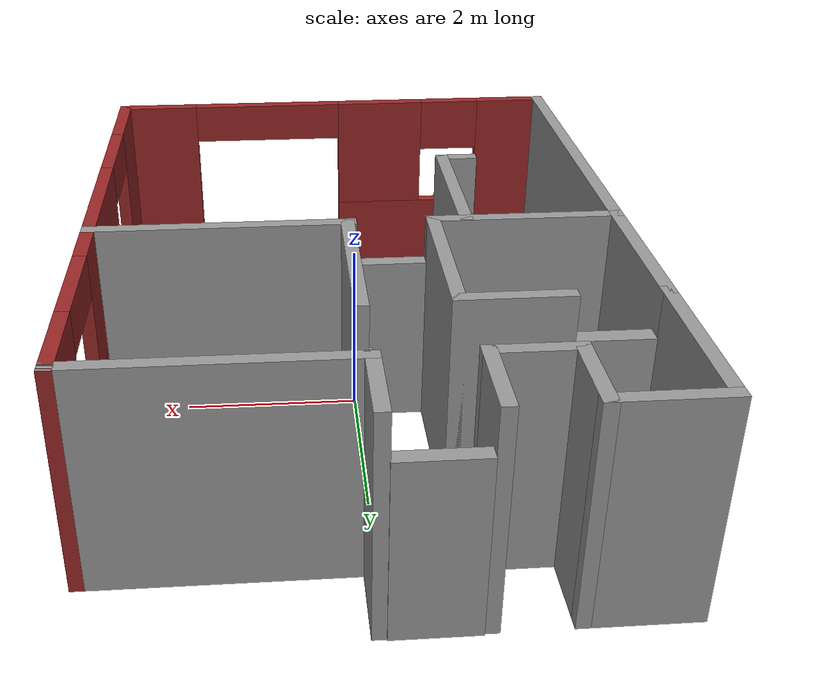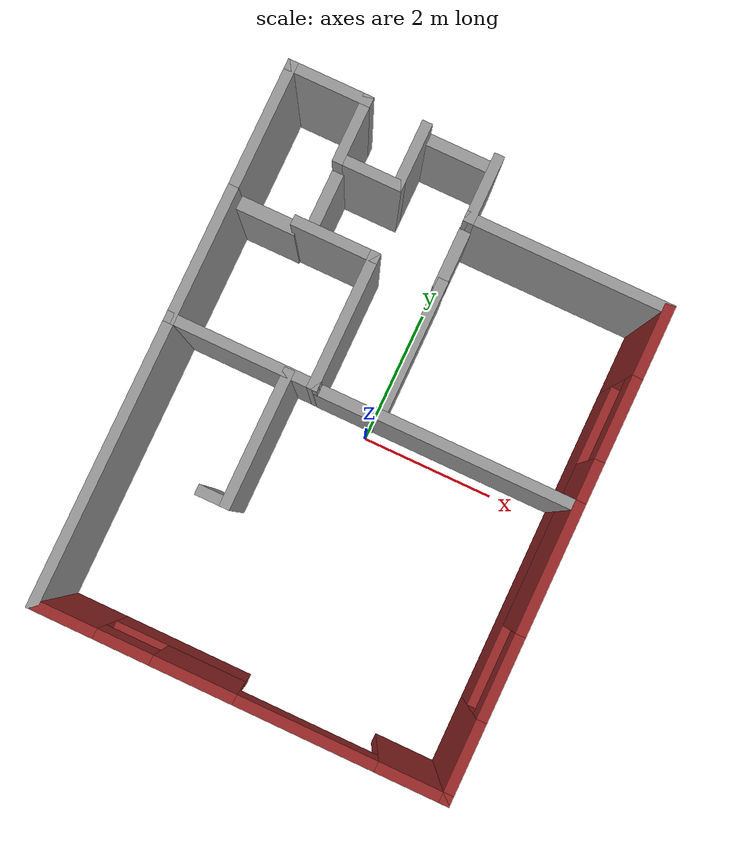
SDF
<?xml version='1.0'?>
<sdf version='1.6'>
  <model name='myroom'>
    <link name='Door_1'>
      <pose frame=''>-0.451398 3.90539 0 0 -0 0</pose>
      <self_collide>0</self_collide>
      <kinematic>0</kinematic>
      <visual name='Door_1_Visual'>
        <pose frame=''>0 0 1 0 -0 0</pose>
        <geometry>
          <box>
            <size>0.9 0.17 2</size>
          </box>
        </geometry>
        <material>
          <script>
            <uri>file://media/materials/scripts/gazebo.material</uri>
            <name>Gazebo/Grey</name>
          </script>
          <ambient>0.3 0.3 0.3 1</ambient>
          <diffuse>0.7 0.7 0.7 1</diffuse>
          <specular>0.01 0.01 0.01 1</specular>
          <emissive>0 0 0 1</emissive>
        </material>
        <transparency>0</transparency>
        <cast_shadows>1</cast_shadows>
      </visual>
      <collision name='Door_1_Collision'>
        <laser_retro>0</laser_retro>
        <max_contacts>10</max_contacts>
        <pose frame=''>0 0 1 0 -0 0</pose>
        <geometry>
          <box>
            <size>0.9 0.17 2</size>
          </box>
        </geometry>
        <surface>
          <friction>
            <ode>
              <mu>1</mu>
              <mu2>1</mu2>
              <fdir1>0 0 0</fdir1>
              <slip1>0</slip1>
              <slip2>0</slip2>
            </ode>
            <torsional>
              <coefficient>1</coefficient>
              <patch_radius>0</patch_radius>
              <surface_radius>0</surface_radius>
              <use_patch_radius>1</use_patch_radius>
              <ode>
                <slip>0</slip>
              </ode>
            </torsional>
          </friction>
          <bounce>
            <restitution_coefficient>0</restitution_coefficient>
            <threshold>1e+06</threshold>
          </bounce>
          <contact>
            <collide_without_contact>0</collide_without_contact>
            <collide_without_contact_bitmask>1</collide_without_contact_bitmask>
            <collide_bitmask>1</collide_bitmask>
            <ode>
              <soft_cfm>0</soft_cfm>
              <soft_erp>0.2</soft_erp>
              <kp>1e+13</kp>
              <kd>1</kd>
              <max_vel>0.01</max_vel>
              <min_depth>0</min_depth>
            </ode>
            <bullet>
              <split_impulse>1</split_impulse>
              <split_impulse_penetration_threshold>-0.01</split_impulse_penetration_threshold>
              <soft_cfm>0</soft_cfm>
              <soft_erp>0.2</soft_erp>
              <kp>1e+13</kp>
              <kd>1</kd>
            </bullet>
          </contact>
        </surface>
      </collision>
    </link>
    <link name='Door_3'>
      <pose frame=''>-1.81536 2.52371 0 0 -0 1.571</pose>
      <self_collide>0</self_collide>
      <kinematic>0</kinematic>
      <visual name='Door_3_Visual'>
        <pose frame=''>0 0 1 0 -0 0</pose>
        <geometry>
          <box>
            <size>0.9 0.17 2</size>
          </box>
        </geometry>
        <material>
          <script>
            <uri>file://media/materials/scripts/gazebo.material</uri>
            <name>Gazebo/Grey</name>
          </script>
          <ambient>0.3 0.3 0.3 1</ambient>
          <diffuse>0.7 0.7 0.7 1</diffuse>
          <specular>0.01 0.01 0.01 1</specular>
          <emissive>0 0 0 1</emissive>
        </material>
        <transparency>0</transparency>
        <cast_shadows>1</cast_shadows>
      </visual>
      <collision name='Door_3_Collision'>
        <laser_retro>0</laser_retro>
        <max_contacts>10</max_contacts>
        <pose frame=''>0 0 1 0 -0 0</pose>
        <geometry>
          <box>
            <size>0.9 0.17 2</size>
          </box>
        </geometry>
        <surface>
          <friction>
            <ode>
              <mu>1</mu>
              <mu2>1</mu2>
              <fdir1>0 0 0</fdir1>
              <slip1>0</slip1>
              <slip2>0</slip2>
            </ode>
            <torsional>
              <coefficient>1</coefficient>
              <patch_radius>0</patch_radius>
              <surface_radius>0</surface_radius>
              <use_patch_radius>1</use_patch_radius>
              <ode>
                <slip>0</slip>
              </ode>
            </torsional>
          </friction>
          <bounce>
            <restitution_coefficient>0</restitution_coefficient>
            <threshold>1e+06</threshold>
          </bounce>
          <contact>
            <collide_without_contact>0</collide_without_contact>
            <collide_without_contact_bitmask>1</collide_without_contact_bitmask>
            <collide_bitmask>1</collide_bitmask>
            <ode>
              <soft_cfm>0</soft_cfm>
              <soft_erp>0.2</soft_erp>
              <kp>1e+13</kp>
              <kd>1</kd>
              <max_vel>0.01</max_vel>
              <min_depth>0</min_depth>
            </ode>
            <bullet>
              <split_impulse>1</split_impulse>
              <split_impulse_penetration_threshold>-0.01</split_impulse_penetration_threshold>
              <soft_cfm>0</soft_cfm>
              <soft_erp>0.2</soft_erp>
              <kp>1e+13</kp>
              <kd>1</kd>
            </bullet>
          </contact>
        </surface>
      </collision>
    </link>
    <link name='Door_4'>
      <pose frame=''>-2.4307 2.04461 0 0 -0 0</pose>
      <self_collide>0</self_collide>
      <kinematic>0</kinematic>
      <visual name='Door_4_Visual'>
        <pose frame=''>0 0 1 0 -0 0</pose>
        <geometry>
          <box>
            <size>0.877571 0.2 2</size>
          </box>
        </geometry>
        <material>
          <script>
            <uri>file://media/materials/scripts/gazebo.material</uri>
            <name>Gazebo/Grey</name>
          </script>
          <ambient>0.3 0.3 0.3 1</ambient>
          <diffuse>0.7 0.7 0.7 1</diffuse>
          <specular>0.01 0.01 0.01 1</specular>
          <emissive>0 0 0 1</emissive>
        </material>
        <transparency>0</transparency>
        <cast_shadows>1</cast_shadows>
      </visual>
      <collision name='Door_4_Collision'>
        <laser_retro>0</laser_retro>
        <max_contacts>10</max_contacts>
        <pose frame=''>0 0 1 0 -0 0</pose>
        <geometry>
          <box>
            <size>0.877571 0.2 2</size>
          </box>
        </geometry>
        <surface>
          <friction>
            <ode>
              <mu>1</mu>
              <mu2>1</mu2>
              <fdir1>0 0 0</fdir1>
              <slip1>0</slip1>
              <slip2>0</slip2>
            </ode>
            <torsional>
              <coefficient>1</coefficient>
              <patch_radius>0</patch_radius>
              <surface_radius>0</surface_radius>
              <use_patch_radius>1</use_patch_radius>
              <ode>
                <slip>0</slip>
              </ode>
            </torsional>
          </friction>
          <bounce>
            <restitution_coefficient>0</restitution_coefficient>
            <threshold>1e+06</threshold>
          </bounce>
          <contact>
            <collide_without_contact>0</collide_without_contact>
            <collide_without_contact_bitmask>1</collide_without_contact_bitmask>
            <collide_bitmask>1</collide_bitmask>
            <ode>
              <soft_cfm>0</soft_cfm>
              <soft_erp>0.2</soft_erp>
              <kp>1e+13</kp>
              <kd>1</kd>
              <max_vel>0.01</max_vel>
              <min_depth>0</min_depth>
            </ode>
            <bullet>
              <split_impulse>1</split_impulse>
              <split_impulse_penetration_threshold>-0.01</split_impulse_penetration_threshold>
              <soft_cfm>0</soft_cfm>
              <soft_erp>0.2</soft_erp>
              <kp>1e+13</kp>
              <kd>1</kd>
            </bullet>
          </contact>
        </surface>
      </collision>
    </link>
    <link name='Door_5'>
      <pose frame=''>0.069335 2.55262 0 0 -0 1.57282</pose>
      <self_collide>0</self_collide>
      <kinematic>0</kinematic>
      <visual name='Door_5_Visual'>
        <pose frame=''>0 0 1 0 -0 0</pose>
        <geometry>
          <box>
            <size>0.9 0.17 2</size>
          </box>
        </geometry>
        <material>
          <script>
            <uri>file://media/materials/scripts/gazebo.material</uri>
            <name>Gazebo/Grey</name>
          </script>
          <ambient>0.3 0.3 0.3 1</ambient>
          <diffuse>0.7 0.7 0.7 1</diffuse>
          <specular>0.01 0.01 0.01 1</specular>
          <emissive>0 0 0 1</emissive>
        </material>
        <transparency>0</transparency>
        <cast_shadows>1</cast_shadows>
      </visual>
      <collision name='Door_5_Collision'>
        <laser_retro>0</laser_retro>
        <max_contacts>10</max_contacts>
        <pose frame=''>0 0 1 0 -0 0</pose>
        <geometry>
          <box>
            <size>0.9 0.17 2</size>
          </box>
        </geometry>
        <surface>
          <friction>
            <ode>
              <mu>1</mu>
              <mu2>1</mu2>
              <fdir1>0 0 0</fdir1>
              <slip1>0</slip1>
              <slip2>0</slip2>
            </ode>
            <torsional>
              <coefficient>1</coefficient>
              <patch_radius>0</patch_radius>
              <surface_radius>0</surface_radius>
              <use_patch_radius>1</use_patch_radius>
              <ode>
                <slip>0</slip>
              </ode>
            </torsional>
          </friction>
          <bounce>
            <restitution_coefficient>0</restitution_coefficient>
            <threshold>1e+06</threshold>
          </bounce>
          <contact>
            <collide_without_contact>0</collide_without_contact>
            <collide_without_contact_bitmask>1</collide_without_contact_bitmask>
            <collide_bitmask>1</collide_bitmask>
            <ode>
              <soft_cfm>0</soft_cfm>
              <soft_erp>0.2</soft_erp>
              <kp>1e+13</kp>
              <kd>1</kd>
              <max_vel>0.01</max_vel>
              <min_depth>0</min_depth>
            </ode>
            <bullet>
              <split_impulse>1</split_impulse>
              <split_impulse_penetration_threshold>-0.01</split_impulse_penetration_threshold>
              <soft_cfm>0</soft_cfm>
              <soft_erp>0.2</soft_erp>
              <kp>1e+13</kp>
              <kd>1</kd>
            </bullet>
          </contact>
        </surface>
      </collision>
    </link>
    <link name='Door_6'>
      <pose frame=''>-0.397625 0.202673 0 0 -0 0</pose>
      <self_collide>0</self_collide>
      <kinematic>0</kinematic>
      <visual name='Door_6_Visual'>
        <pose frame=''>0 0 1 0 -0 0</pose>
        <geometry>
          <box>
            <size>0.9 0.17 2</size>
          </box>
        </geometry>
        <material>
          <script>
            <uri>file://media/materials/scripts/gazebo.material</uri>
            <name>Gazebo/Grey</name>
          </script>
          <ambient>0.3 0.3 0.3 1</ambient>
          <diffuse>0.7 0.7 0.7 1</diffuse>
          <specular>0.01 0.01 0.01 1</specular>
          <emissive>0 0 0 1</emissive>
        </material>
        <transparency>0</transparency>
        <cast_shadows>1</cast_shadows>
      </visual>
      <collision name='Door_6_Collision'>
        <laser_retro>0</laser_retro>
        <max_contacts>10</max_contacts>
        <pose frame=''>0 0 1 0 -0 0</pose>
        <geometry>
          <box>
            <size>0.9 0.17 2</size>
          </box>
        </geometry>
        <surface>
          <friction>
            <ode>
              <mu>1</mu>
              <mu2>1</mu2>
              <fdir1>0 0 0</fdir1>
              <slip1>0</slip1>
              <slip2>0</slip2>
            </ode>
            <torsional>
              <coefficient>1</coefficient>
              <patch_radius>0</patch_radius>
              <surface_radius>0</surface_radius>
              <use_patch_radius>1</use_patch_radius>
              <ode>
                <slip>0</slip>
              </ode>
            </torsional>
          </friction>
          <bounce>
            <restitution_coefficient>0</restitution_coefficient>
            <threshold>1e+06</threshold>
          </bounce>
          <contact>
            <collide_without_contact>0</collide_without_contact>
            <collide_without_contact_bitmask>1</collide_without_contact_bitmask>
            <collide_bitmask>1</collide_bitmask>
            <ode>
              <soft_cfm>0</soft_cfm>
              <soft_erp>0.2</soft_erp>
              <kp>1e+13</kp>
              <kd>1</kd>
              <max_vel>0.01</max_vel>
              <min_depth>0</min_depth>
            </ode>
            <bullet>
              <split_impulse>1</split_impulse>
              <split_impulse_penetration_threshold>-0.01</split_impulse_penetration_threshold>
              <soft_cfm>0</soft_cfm>
              <soft_erp>0.2</soft_erp>
              <kp>1e+13</kp>
              <kd>1</kd>
            </bullet>
          </contact>
        </surface>
      </collision>
    </link>
    <link name='Wall_1'>
      <pose frame=''>0.068128 3.47648 0 0 0 -1.5708</pose>
      <self_collide>0</self_collide>
      <kinematic>0</kinematic>
      <visual name='Wall_1_Visual'>
        <pose frame=''>0 0 1.25 0 -0 0</pose>
        <geometry>
          <box>
            <size>1 0.15 2.5</size>
          </box>
        </geometry>
        <material>
          <script>
            <uri>file://media/materials/scripts/gazebo.material</uri>
            <name>Gazebo/Grey</name>
          </script>
          <ambient>1 1 1 1</ambient>
          <diffuse>0.7 0.7 0.7 1</diffuse>
          <specular>0.01 0.01 0.01 1</specular>
          <emissive>0 0 0 1</emissive>
        </material>
        <meta>
          <layer>0</layer>
        </meta>
        <transparency>0</transparency>
        <cast_shadows>1</cast_shadows>
      </visual>
      <collision name='Wall_1_Collision'>
        <laser_retro>0</laser_retro>
        <max_contacts>10</max_contacts>
        <pose frame=''>0 0 1.25 0 -0 0</pose>
        <geometry>
          <box>
            <size>1 0.15 2.5</size>
          </box>
        </geometry>
        <surface>
          <friction>
            <ode>
              <mu>1</mu>
              <mu2>1</mu2>
              <fdir1>0 0 0</fdir1>
              <slip1>0</slip1>
              <slip2>0</slip2>
            </ode>
            <torsional>
              <coefficient>1</coefficient>
              <patch_radius>0</patch_radius>
              <surface_radius>0</surface_radius>
              <use_patch_radius>1</use_patch_radius>
              <ode>
                <slip>0</slip>
              </ode>
            </torsional>
          </friction>
          <bounce>
            <restitution_coefficient>0</restitution_coefficient>
            <threshold>1e+06</threshold>
          </bounce>
          <contact>
            <collide_without_contact>0</collide_without_contact>
            <collide_without_contact_bitmask>1</collide_without_contact_bitmask>
            <collide_bitmask>1</collide_bitmask>
            <ode>
              <soft_cfm>0</soft_cfm>
              <soft_erp>0.2</soft_erp>
              <kp>1e+13</kp>
              <kd>1</kd>
              <max_vel>0.01</max_vel>
              <min_depth>0</min_depth>
            </ode>
            <bullet>
              <split_impulse>1</split_impulse>
              <split_impulse_penetration_threshold>-0.01</split_impulse_penetration_threshold>
              <soft_cfm>0</soft_cfm>
              <soft_erp>0.2</soft_erp>
              <kp>1e+13</kp>
              <kd>1</kd>
            </bullet>
          </contact>
        </surface>
      </collision>
    </link>
    <link name='Wall_10'>
      <pose frame=''>-1.82502 3.47364 0 0 -0 1.5708</pose>
      <self_collide>0</self_collide>
      <kinematic>0</kinematic>
      <visual name='Wall_10_Visual'>
        <pose frame=''>0 0 1.25 0 -0 0</pose>
        <geometry>
          <box>
            <size>1 0.15 2.5</size>
          </box>
        </geometry>
        <material>
          <script>
            <uri>file://media/materials/scripts/gazebo.material</uri>
            <name>Gazebo/Grey</name>
          </script>
          <ambient>1 1 1 1</ambient>
          <diffuse>0.7 0.7 0.7 1</diffuse>
          <specular>0.01 0.01 0.01 1</specular>
          <emissive>0 0 0 1</emissive>
        </material>
        <meta>
          <layer>0</layer>
        </meta>
        <transparency>0</transparency>
        <cast_shadows>1</cast_shadows>
      </visual>
      <collision name='Wall_10_Collision'>
        <laser_retro>0</laser_retro>
        <max_contacts>10</max_contacts>
        <pose frame=''>0 0 1.25 0 -0 0</pose>
        <geometry>
          <box>
            <size>1 0.15 2.5</size>
          </box>
        </geometry>
        <surface>
          <friction>
            <ode>
              <mu>1</mu>
              <mu2>1</mu2>
              <fdir1>0 0 0</fdir1>
              <slip1>0</slip1>
              <slip2>0</slip2>
            </ode>
            <torsional>
              <coefficient>1</coefficient>
              <patch_radius>0</patch_radius>
              <surface_radius>0</surface_radius>
              <use_patch_radius>1</use_patch_radius>
              <ode>
                <slip>0</slip>
              </ode>
            </torsional>
          </friction>
          <bounce>
            <restitution_coefficient>0</restitution_coefficient>
            <threshold>1e+06</threshold>
          </bounce>
          <contact>
            <collide_without_contact>0</collide_without_contact>
            <collide_without_contact_bitmask>1</collide_without_contact_bitmask>
            <collide_bitmask>1</collide_bitmask>
            <ode>
              <soft_cfm>0</soft_cfm>
              <soft_erp>0.2</soft_erp>
              <kp>1e+13</kp>
              <kd>1</kd>
              <max_vel>0.01</max_vel>
              <min_depth>0</min_depth>
            </ode>
            <bullet>
              <split_impulse>1</split_impulse>
              <split_impulse_penetration_threshold>-0.01</split_impulse_penetration_threshold>
              <soft_cfm>0</soft_cfm>
              <soft_erp>0.2</soft_erp>
              <kp>1e+13</kp>
              <kd>1</kd>
            </bullet>
          </contact>
        </surface>
      </collision>
    </link>
    <link name='Wall_14'>
      <pose frame=''>-2.37502 3.89864 0 0 -0 3.14159</pose>
      <self_collide>0</self_collide>
      <kinematic>0</kinematic>
      <visual name='Wall_14_Visual'>
        <pose frame=''>0 0 1.25 0 -0 0</pose>
        <geometry>
          <box>
            <size>1.25 0.15 2.5</size>
          </box>
        </geometry>
        <material>
          <script>
            <uri>file://media/materials/scripts/gazebo.material</uri>
            <name>Gazebo/Grey</name>
          </script>
          <ambient>1 1 1 1</ambient>
          <diffuse>0.7 0.7 0.7 1</diffuse>
          <specular>0.01 0.01 0.01 1</specular>
          <emissive>0 0 0 1</emissive>
        </material>
        <meta>
          <layer>0</layer>
        </meta>
        <transparency>0</transparency>
        <cast_shadows>1</cast_shadows>
      </visual>
      <collision name='Wall_14_Collision'>
        <laser_retro>0</laser_retro>
        <max_contacts>10</max_contacts>
        <pose frame=''>0 0 1.25 0 -0 0</pose>
        <geometry>
          <box>
            <size>1.25 0.15 2.5</size>
          </box>
        </geometry>
        <surface>
          <friction>
            <ode>
              <mu>1</mu>
              <mu2>1</mu2>
              <fdir1>0 0 0</fdir1>
              <slip1>0</slip1>
              <slip2>0</slip2>
            </ode>
            <torsional>
              <coefficient>1</coefficient>
              <patch_radius>0</patch_radius>
              <surface_radius>0</surface_radius>
              <use_patch_radius>1</use_patch_radius>
              <ode>
                <slip>0</slip>
              </ode>
            </torsional>
          </friction>
          <bounce>
            <restitution_coefficient>0</restitution_coefficient>
            <threshold>1e+06</threshold>
          </bounce>
          <contact>
            <collide_without_contact>0</collide_without_contact>
            <collide_without_contact_bitmask>1</collide_without_contact_bitmask>
            <collide_bitmask>1</collide_bitmask>
            <ode>
              <soft_cfm>0</soft_cfm>
              <soft_erp>0.2</soft_erp>
              <kp>1e+13</kp>
              <kd>1</kd>
              <max_vel>0.01</max_vel>
              <min_depth>0</min_depth>
            </ode>
            <bullet>
              <split_impulse>1</split_impulse>
              <split_impulse_penetration_threshold>-0.01</split_impulse_penetration_threshold>
              <soft_cfm>0</soft_cfm>
              <soft_erp>0.2</soft_erp>
              <kp>1e+13</kp>
              <kd>1</kd>
            </bullet>
          </contact>
        </surface>
      </collision>
    </link>
    <link name='Wall_16'>
      <pose frame=''>-2.92502 2.97364 0 0 0 -1.5708</pose>
      <self_collide>0</self_collide>
      <kinematic>0</kinematic>
      <visual name='Wall_16_Visual'>
        <pose frame=''>0 0 1.25 0 -0 0</pose>
        <geometry>
          <box>
            <size>2 0.15 2.5</size>
          </box>
        </geometry>
        <material>
          <script>
            <uri>file://media/materials/scripts/gazebo.material</uri>
            <name>Gazebo/Grey</name>
          </script>
          <ambient>1 1 1 1</ambient>
          <diffuse>0.7 0.7 0.7 1</diffuse>
          <specular>0.01 0.01 0.01 1</specular>
          <emissive>0 0 0 1</emissive>
        </material>
        <meta>
          <layer>0</layer>
        </meta>
        <transparency>0</transparency>
        <cast_shadows>1</cast_shadows>
      </visual>
      <collision name='Wall_16_Collision'>
        <laser_retro>0</laser_retro>
        <max_contacts>10</max_contacts>
        <pose frame=''>0 0 1.25 0 -0 0</pose>
        <geometry>
          <box>
            <size>2 0.15 2.5</size>
          </box>
        </geometry>
        <surface>
          <friction>
            <ode>
              <mu>1</mu>
              <mu2>1</mu2>
              <fdir1>0 0 0</fdir1>
              <slip1>0</slip1>
              <slip2>0</slip2>
            </ode>
            <torsional>
              <coefficient>1</coefficient>
              <patch_radius>0</patch_radius>
              <surface_radius>0</surface_radius>
              <use_patch_radius>1</use_patch_radius>
              <ode>
                <slip>0</slip>
              </ode>
            </torsional>
          </friction>
          <bounce>
            <restitution_coefficient>0</restitution_coefficient>
            <threshold>1e+06</threshold>
          </bounce>
          <contact>
            <collide_without_contact>0</collide_without_contact>
            <collide_without_contact_bitmask>1</collide_without_contact_bitmask>
            <collide_bitmask>1</collide_bitmask>
            <ode>
              <soft_cfm>0</soft_cfm>
              <soft_erp>0.2</soft_erp>
              <kp>1e+13</kp>
              <kd>1</kd>
              <max_vel>0.01</max_vel>
              <min_depth>0</min_depth>
            </ode>
            <bullet>
              <split_impulse>1</split_impulse>
              <split_impulse_penetration_threshold>-0.01</split_impulse_penetration_threshold>
              <soft_cfm>0</soft_cfm>
              <soft_erp>0.2</soft_erp>
              <kp>1e+13</kp>
              <kd>1</kd>
            </bullet>
          </contact>
        </surface>
      </collision>
    </link>
    <link name='Wall_20'>
      <pose frame=''>-2.92502 1.12364 0 0 0 -1.5708</pose>
      <self_collide>0</self_collide>
      <kinematic>0</kinematic>
      <visual name='Wall_20_Visual'>
        <pose frame=''>0 0 1.25 0 -0 0</pose>
        <geometry>
          <box>
            <size>2 0.15 2.5</size>
          </box>
        </geometry>
        <material>
          <script>
            <uri>file://media/materials/scripts/gazebo.material</uri>
            <name>Gazebo/Grey</name>
          </script>
          <ambient>1 1 1 1</ambient>
          <diffuse>0.7 0.7 0.7 1</diffuse>
          <specular>0.01 0.01 0.01 1</specular>
          <emissive>0 0 0 1</emissive>
        </material>
        <meta>
          <layer>0</layer>
        </meta>
        <transparency>0</transparency>
        <cast_shadows>1</cast_shadows>
      </visual>
      <collision name='Wall_20_Collision'>
        <laser_retro>0</laser_retro>
        <max_contacts>10</max_contacts>
        <pose frame=''>0 0 1.25 0 -0 0</pose>
        <geometry>
          <box>
            <size>2 0.15 2.5</size>
          </box>
        </geometry>
        <surface>
          <friction>
            <ode>
              <mu>1</mu>
              <mu2>1</mu2>
              <fdir1>0 0 0</fdir1>
              <slip1>0</slip1>
              <slip2>0</slip2>
            </ode>
            <torsional>
              <coefficient>1</coefficient>
              <patch_radius>0</patch_radius>
              <surface_radius>0</surface_radius>
              <use_patch_radius>1</use_patch_radius>
              <ode>
                <slip>0</slip>
              </ode>
            </torsional>
          </friction>
          <bounce>
            <restitution_coefficient>0</restitution_coefficient>
            <threshold>1e+06</threshold>
          </bounce>
          <contact>
            <collide_without_contact>0</collide_without_contact>
            <collide_without_contact_bitmask>1</collide_without_contact_bitmask>
            <collide_bitmask>1</collide_bitmask>
            <ode>
              <soft_cfm>0</soft_cfm>
              <soft_erp>0.2</soft_erp>
              <kp>1e+13</kp>
              <kd>1</kd>
              <max_vel>0.01</max_vel>
              <min_depth>0</min_depth>
            </ode>
            <bullet>
              <split_impulse>1</split_impulse>
              <split_impulse_penetration_threshold>-0.01</split_impulse_penetration_threshold>
              <soft_cfm>0</soft_cfm>
              <soft_erp>0.2</soft_erp>
              <kp>1e+13</kp>
              <kd>1</kd>
            </bullet>
          </contact>
        </surface>
      </collision>
    </link>
    <link name='Wall_27'>
      <pose frame=''>-1.40928 2.04626 0 0 -0 0</pose>
      <self_collide>0</self_collide>
      <kinematic>0</kinematic>
      <visual name='Wall_27_Visual'>
        <pose frame=''>0 0 1.25 0 -0 0</pose>
        <geometry>
          <box>
            <size>1.25 0.15 2.5</size>
          </box>
        </geometry>
        <material>
          <script>
            <uri>file://media/materials/scripts/gazebo.material</uri>
            <name>Gazebo/Grey</name>
          </script>
          <ambient>1 1 1 1</ambient>
          <diffuse>0.7 0.7 0.7 1</diffuse>
          <specular>0.01 0.01 0.01 1</specular>
          <emissive>0 0 0 1</emissive>
        </material>
        <meta>
          <layer>0</layer>
        </meta>
        <transparency>0</transparency>
        <cast_shadows>1</cast_shadows>
      </visual>
      <collision name='Wall_27_Collision'>
        <laser_retro>0</laser_retro>
        <max_contacts>10</max_contacts>
        <pose frame=''>0 0 1.25 0 -0 0</pose>
        <geometry>
          <box>
            <size>1.25 0.15 2.5</size>
          </box>
        </geometry>
        <surface>
          <friction>
            <ode>
              <mu>1</mu>
              <mu2>1</mu2>
              <fdir1>0 0 0</fdir1>
              <slip1>0</slip1>
              <slip2>0</slip2>
            </ode>
            <torsional>
              <coefficient>1</coefficient>
              <patch_radius>0</patch_radius>
              <surface_radius>0</surface_radius>
              <use_patch_radius>1</use_patch_radius>
              <ode>
                <slip>0</slip>
              </ode>
            </torsional>
          </friction>
          <bounce>
            <restitution_coefficient>0</restitution_coefficient>
            <threshold>1e+06</threshold>
          </bounce>
          <contact>
            <collide_without_contact>0</collide_without_contact>
            <collide_without_contact_bitmask>1</collide_without_contact_bitmask>
            <collide_bitmask>1</collide_bitmask>
            <ode>
              <soft_cfm>0</soft_cfm>
              <soft_erp>0.2</soft_erp>
              <kp>1e+13</kp>
              <kd>1</kd>
              <max_vel>0.01</max_vel>
              <min_depth>0</min_depth>
            </ode>
            <bullet>
              <split_impulse>1</split_impulse>
              <split_impulse_penetration_threshold>-0.01</split_impulse_penetration_threshold>
              <soft_cfm>0</soft_cfm>
              <soft_erp>0.2</soft_erp>
              <kp>1e+13</kp>
              <kd>1</kd>
            </bullet>
          </contact>
        </surface>
      </collision>
    </link>
    <link name='Wall_28'>
      <pose frame=''>-0.859282 1.12126 0 0 0 -1.5708</pose>
      <self_collide>0</self_collide>
      <kinematic>0</kinematic>
      <visual name='Wall_28_Visual'>
        <pose frame=''>0 0 1.25 0 -0 0</pose>
        <geometry>
          <box>
            <size>2 0.15 2.5</size>
          </box>
        </geometry>
        <material>
          <script>
            <uri>file://media/materials/scripts/gazebo.material</uri>
            <name>Gazebo/Grey</name>
          </script>
          <ambient>1 1 1 1</ambient>
          <diffuse>0.7 0.7 0.7 1</diffuse>
          <specular>0.01 0.01 0.01 1</specular>
          <emissive>0 0 0 1</emissive>
        </material>
        <meta>
          <layer>0</layer>
        </meta>
        <transparency>0</transparency>
        <cast_shadows>1</cast_shadows>
      </visual>
      <collision name='Wall_28_Collision'>
        <laser_retro>0</laser_retro>
        <max_contacts>10</max_contacts>
        <pose frame=''>0 0 1.25 0 -0 0</pose>
        <geometry>
          <box>
            <size>2 0.15 2.5</size>
          </box>
        </geometry>
        <surface>
          <friction>
            <ode>
              <mu>1</mu>
              <mu2>1</mu2>
              <fdir1>0 0 0</fdir1>
              <slip1>0</slip1>
              <slip2>0</slip2>
            </ode>
            <torsional>
              <coefficient>1</coefficient>
              <patch_radius>0</patch_radius>
              <surface_radius>0</surface_radius>
              <use_patch_radius>1</use_patch_radius>
              <ode>
                <slip>0</slip>
              </ode>
            </torsional>
          </friction>
          <bounce>
            <restitution_coefficient>0</restitution_coefficient>
            <threshold>1e+06</threshold>
          </bounce>
          <contact>
            <collide_without_contact>0</collide_without_contact>
            <collide_without_contact_bitmask>1</collide_without_contact_bitmask>
            <collide_bitmask>1</collide_bitmask>
            <ode>
              <soft_cfm>0</soft_cfm>
              <soft_erp>0.2</soft_erp>
              <kp>1e+13</kp>
              <kd>1</kd>
              <max_vel>0.01</max_vel>
              <min_depth>0</min_depth>
            </ode>
            <bullet>
              <split_impulse>1</split_impulse>
              <split_impulse_penetration_threshold>-0.01</split_impulse_penetration_threshold>
              <soft_cfm>0</soft_cfm>
              <soft_erp>0.2</soft_erp>
              <kp>1e+13</kp>
              <kd>1</kd>
            </bullet>
          </contact>
        </surface>
      </collision>
    </link>
    <link name='Wall_3'>
      <pose frame=''>-0.975019 3.47364 0 0 0 -1.5708</pose>
      <self_collide>0</self_collide>
      <kinematic>0</kinematic>
      <visual name='Wall_3_Visual'>
        <pose frame=''>0 0 1.25 0 -0 0</pose>
        <geometry>
          <box>
            <size>1 0.15 2.5</size>
          </box>
        </geometry>
        <material>
          <script>
            <uri>file://media/materials/scripts/gazebo.material</uri>
            <name>Gazebo/Grey</name>
          </script>
          <ambient>1 1 1 1</ambient>
          <diffuse>0.7 0.7 0.7 1</diffuse>
          <specular>0.01 0.01 0.01 1</specular>
          <emissive>0 0 0 1</emissive>
        </material>
        <meta>
          <layer>0</layer>
        </meta>
        <transparency>0</transparency>
        <cast_shadows>1</cast_shadows>
      </visual>
      <collision name='Wall_3_Collision'>
        <laser_retro>0</laser_retro>
        <max_contacts>10</max_contacts>
        <pose frame=''>0 0 1.25 0 -0 0</pose>
        <geometry>
          <box>
            <size>1 0.15 2.5</size>
          </box>
        </geometry>
        <surface>
          <friction>
            <ode>
              <mu>1</mu>
              <mu2>1</mu2>
              <fdir1>0 0 0</fdir1>
              <slip1>0</slip1>
              <slip2>0</slip2>
            </ode>
            <torsional>
              <coefficient>1</coefficient>
              <patch_radius>0</patch_radius>
              <surface_radius>0</surface_radius>
              <use_patch_radius>1</use_patch_radius>
              <ode>
                <slip>0</slip>
              </ode>
            </torsional>
          </friction>
          <bounce>
            <restitution_coefficient>0</restitution_coefficient>
            <threshold>1e+06</threshold>
          </bounce>
          <contact>
            <collide_without_contact>0</collide_without_contact>
            <collide_without_contact_bitmask>1</collide_without_contact_bitmask>
            <collide_bitmask>1</collide_bitmask>
            <ode>
              <soft_cfm>0</soft_cfm>
              <soft_erp>0.2</soft_erp>
              <kp>1e+13</kp>
              <kd>1</kd>
              <max_vel>0.01</max_vel>
              <min_depth>0</min_depth>
            </ode>
            <bullet>
              <split_impulse>1</split_impulse>
              <split_impulse_penetration_threshold>-0.01</split_impulse_penetration_threshold>
              <soft_cfm>0</soft_cfm>
              <soft_erp>0.2</soft_erp>
              <kp>1e+13</kp>
              <kd>1</kd>
            </bullet>
          </contact>
        </surface>
      </collision>
    </link>
    <link name='Wall_31'>
      <pose frame=''>0.092728 1.16063 0 0 0 -1.5708</pose>
      <self_collide>0</self_collide>
      <kinematic>0</kinematic>
      <visual name='Wall_31_Visual'>
        <pose frame=''>0 0 1.25 0 -0 0</pose>
        <geometry>
          <box>
            <size>2 0.15 2.5</size>
          </box>
        </geometry>
        <material>
          <script>
            <uri>file://media/materials/scripts/gazebo.material</uri>
            <name>Gazebo/Grey</name>
          </script>
          <ambient>1 1 1 1</ambient>
          <diffuse>0.7 0.7 0.7 1</diffuse>
          <specular>0.01 0.01 0.01 1</specular>
          <emissive>0 0 0 1</emissive>
        </material>
        <meta>
          <layer>0</layer>
        </meta>
        <transparency>0</transparency>
        <cast_shadows>1</cast_shadows>
      </visual>
      <collision name='Wall_31_Collision'>
        <laser_retro>0</laser_retro>
        <max_contacts>10</max_contacts>
        <pose frame=''>0 0 1.25 0 -0 0</pose>
        <geometry>
          <box>
            <size>2 0.15 2.5</size>
          </box>
        </geometry>
        <surface>
          <friction>
            <ode>
              <mu>1</mu>
              <mu2>1</mu2>
              <fdir1>0 0 0</fdir1>
              <slip1>0</slip1>
              <slip2>0</slip2>
            </ode>
            <torsional>
              <coefficient>1</coefficient>
              <patch_radius>0</patch_radius>
              <surface_radius>0</surface_radius>
              <use_patch_radius>1</use_patch_radius>
              <ode>
                <slip>0</slip>
              </ode>
            </torsional>
          </friction>
          <bounce>
            <restitution_coefficient>0</restitution_coefficient>
            <threshold>1e+06</threshold>
          </bounce>
          <contact>
            <collide_without_contact>0</collide_without_contact>
            <collide_without_contact_bitmask>1</collide_without_contact_bitmask>
            <collide_bitmask>1</collide_bitmask>
            <ode>
              <soft_cfm>0</soft_cfm>
              <soft_erp>0.2</soft_erp>
              <kp>1e+13</kp>
              <kd>1</kd>
              <max_vel>0.01</max_vel>
              <min_depth>0</min_depth>
            </ode>
            <bullet>
              <split_impulse>1</split_impulse>
              <split_impulse_penetration_threshold>-0.01</split_impulse_penetration_threshold>
              <soft_cfm>0</soft_cfm>
              <soft_erp>0.2</soft_erp>
              <kp>1e+13</kp>
              <kd>1</kd>
            </bullet>
          </contact>
        </surface>
      </collision>
    </link>
    <link name='Wall_34'>
      <pose frame=''>1.49313 3.05148 0 0 -0 0</pose>
      <self_collide>0</self_collide>
      <kinematic>0</kinematic>
      <visual name='Wall_34_Visual'>
        <pose frame=''>0 0 1.25 0 -0 0</pose>
        <geometry>
          <box>
            <size>3 0.15 2.5</size>
          </box>
        </geometry>
        <material>
          <script>
            <uri>file://media/materials/scripts/gazebo.material</uri>
            <name>Gazebo/Grey</name>
          </script>
          <ambient>1 1 1 1</ambient>
          <diffuse>0.7 0.7 0.7 1</diffuse>
          <specular>0.01 0.01 0.01 1</specular>
          <emissive>0 0 0 1</emissive>
        </material>
        <meta>
          <layer>0</layer>
        </meta>
        <transparency>0</transparency>
        <cast_shadows>1</cast_shadows>
      </visual>
      <collision name='Wall_34_Collision'>
        <laser_retro>0</laser_retro>
        <max_contacts>10</max_contacts>
        <pose frame=''>0 0 1.25 0 -0 0</pose>
        <geometry>
          <box>
            <size>3 0.15 2.5</size>
          </box>
        </geometry>
        <surface>
          <friction>
            <ode>
              <mu>1</mu>
              <mu2>1</mu2>
              <fdir1>0 0 0</fdir1>
              <slip1>0</slip1>
              <slip2>0</slip2>
            </ode>
            <torsional>
              <coefficient>1</coefficient>
              <patch_radius>0</patch_radius>
              <surface_radius>0</surface_radius>
              <use_patch_radius>1</use_patch_radius>
              <ode>
                <slip>0</slip>
              </ode>
            </torsional>
          </friction>
          <bounce>
            <restitution_coefficient>0</restitution_coefficient>
            <threshold>1e+06</threshold>
          </bounce>
          <contact>
            <collide_without_contact>0</collide_without_contact>
            <collide_without_contact_bitmask>1</collide_without_contact_bitmask>
            <collide_bitmask>1</collide_bitmask>
            <ode>
              <soft_cfm>0</soft_cfm>
              <soft_erp>0.2</soft_erp>
              <kp>1e+13</kp>
              <kd>1</kd>
              <max_vel>0.01</max_vel>
              <min_depth>0</min_depth>
            </ode>
            <bullet>
              <split_impulse>1</split_impulse>
              <split_impulse_penetration_threshold>-0.01</split_impulse_penetration_threshold>
              <soft_cfm>0</soft_cfm>
              <soft_erp>0.2</soft_erp>
              <kp>1e+13</kp>
              <kd>1</kd>
            </bullet>
          </contact>
        </surface>
      </collision>
    </link>
    <link name='Wall_35'>
      <pose frame=''>2.91813 1.62648 0 0 0 -1.5708</pose>
      <self_collide>0</self_collide>
      <kinematic>0</kinematic>
      <gravity>1</gravity>
      <inertial>
        <mass>1</mass>
        <pose frame=''>0 0 0 0 -0 0</pose>
        <inertia>
          <ixx>1</ixx>
          <ixy>0</ixy>
          <ixz>0</ixz>
          <iyy>1</iyy>
          <iyz>0</iyz>
          <izz>1</izz>
        </inertia>
      </inertial>
      <visual name='Wall_35_Visual_0'>
        <pose frame=''>-0.967837 0 1.25 0 -0 0</pose>
        <geometry>
          <box>
            <size>1.06433 0.15 2.5</size>
          </box>
        </geometry>
        <material>
          <script>
            <uri>file://media/materials/scripts/gazebo.material</uri>
            <name>Gazebo/Grey</name>
          </script>
          <ambient>0.6 0.15 0.15 1</ambient>
          <diffuse>0.7 0.7 0.7 1</diffuse>
          <specular>0.01 0.01 0.01 1</specular>
          <emissive>0 0 0 1</emissive>
          <shader type='vertex'>
            <normal_map>__default__</normal_map>
          </shader>
        </material>
        <meta>
          <layer>0</layer>
        </meta>
        <transparency>0</transparency>
        <cast_shadows>1</cast_shadows>
      </visual>
      <visual name='Wall_35_Visual_1'>
        <pose frame=''>0.532163 0 0.5 0 -0 0</pose>
        <geometry>
          <box>
            <size>1.93567 0.15 1</size>
          </box>
        </geometry>
        <material>
          <script>
            <uri>file://media/materials/scripts/gazebo.material</uri>
            <name>Gazebo/Grey</name>
          </script>
          <ambient>0.6 0.15 0.15 1</ambient>
          <diffuse>0.7 0.7 0.7 1</diffuse>
          <specular>0.01 0.01 0.01 1</specular>
          <emissive>0 0 0 1</emissive>
          <shader type='vertex'>
            <normal_map>__default__</normal_map>
          </shader>
        </material>
        <meta>
          <layer>0</layer>
        </meta>
        <transparency>0</transparency>
        <cast_shadows>1</cast_shadows>
      </visual>
      <visual name='Wall_35_Visual_2'>
        <pose frame=''>1.13216 0 1.75 0 -0 0</pose>
        <geometry>
          <box>
            <size>0.735674 0.15 1.5</size>
          </box>
        </geometry>
        <material>
          <script>
            <uri>file://media/materials/scripts/gazebo.material</uri>
            <name>Gazebo/Grey</name>
          </script>
          <ambient>0.6 0.15 0.15 1</ambient>
          <diffuse>0.7 0.7 0.7 1</diffuse>
          <specular>0.01 0.01 0.01 1</specular>
          <emissive>0 0 0 1</emissive>
          <shader type='vertex'>
            <normal_map>__default__</normal_map>
          </shader>
        </material>
        <meta>
          <layer>0</layer>
        </meta>
        <transparency>0</transparency>
        <cast_shadows>1</cast_shadows>
      </visual>
      <visual name='Wall_35_Visual_3'>
        <pose frame=''>0.164326 0 2.25 0 -0 0</pose>
        <geometry>
          <box>
            <size>1.2 0.15 0.5</size>
          </box>
        </geometry>
        <material>
          <script>
            <uri>file://media/materials/scripts/gazebo.material</uri>
            <name>Gazebo/Grey</name>
          </script>
          <ambient>0.6 0.15 0.15 1</ambient>
          <diffuse>0.7 0.7 0.7 1</diffuse>
          <specular>0.01 0.01 0.01 1</specular>
          <emissive>0 0 0 1</emissive>
          <shader type='vertex'>
            <normal_map>__default__</normal_map>
          </shader>
        </material>
        <meta>
          <layer>0</layer>
        </meta>
        <transparency>0</transparency>
        <cast_shadows>1</cast_shadows>
      </visual>
      <collision name='Wall_35_Collision_0'>
        <laser_retro>0</laser_retro>
        <max_contacts>10</max_contacts>
        <pose frame=''>-0.967837 0 1.25 0 -0 0</pose>
        <geometry>
          <box>
            <size>1.06433 0.15 2.5</size>
          </box>
        </geometry>
        <surface>
          <friction>
            <ode>
              <mu>1</mu>
              <mu2>1</mu2>
              <fdir1>0 0 0</fdir1>
              <slip1>0</slip1>
              <slip2>0</slip2>
            </ode>
            <torsional>
              <coefficient>1</coefficient>
              <patch_radius>0</patch_radius>
              <surface_radius>0</surface_radius>
              <use_patch_radius>1</use_patch_radius>
              <ode>
                <slip>0</slip>
              </ode>
            </torsional>
          </friction>
          <bounce>
            <restitution_coefficient>0</restitution_coefficient>
            <threshold>1e+06</threshold>
          </bounce>
          <contact>
            <collide_without_contact>0</collide_without_contact>
            <collide_without_contact_bitmask>1</collide_without_contact_bitmask>
            <collide_bitmask>1</collide_bitmask>
            <ode>
              <soft_cfm>0</soft_cfm>
              <soft_erp>0.2</soft_erp>
              <kp>1e+13</kp>
              <kd>1</kd>
              <max_vel>0.01</max_vel>
              <min_depth>0</min_depth>
            </ode>
            <bullet>
              <split_impulse>1</split_impulse>
              <split_impulse_penetration_threshold>-0.01</split_impulse_penetration_threshold>
              <soft_cfm>0</soft_cfm>
              <soft_erp>0.2</soft_erp>
              <kp>1e+13</kp>
              <kd>1</kd>
            </bullet>
          </contact>
        </surface>
      </collision>
      <collision name='Wall_35_Collision_1'>
        <laser_retro>0</laser_retro>
        <max_contacts>10</max_contacts>
        <pose frame=''>0.532163 0 0.5 0 -0 0</pose>
        <geometry>
          <box>
            <size>1.93567 0.15 1</size>
          </box>
        </geometry>
        <surface>
          <friction>
            <ode>
              <mu>1</mu>
              <mu2>1</mu2>
              <fdir1>0 0 0</fdir1>
              <slip1>0</slip1>
              <slip2>0</slip2>
            </ode>
            <torsional>
              <coefficient>1</coefficient>
              <patch_radius>0</patch_radius>
              <surface_radius>0</surface_radius>
              <use_patch_radius>1</use_patch_radius>
              <ode>
                <slip>0</slip>
              </ode>
            </torsional>
          </friction>
          <bounce>
            <restitution_coefficient>0</restitution_coefficient>
            <threshold>1e+06</threshold>
          </bounce>
          <contact>
            <collide_without_contact>0</collide_without_contact>
            <collide_without_contact_bitmask>1</collide_without_contact_bitmask>
            <collide_bitmask>1</collide_bitmask>
            <ode>
              <soft_cfm>0</soft_cfm>
              <soft_erp>0.2</soft_erp>
              <kp>1e+13</kp>
              <kd>1</kd>
              <max_vel>0.01</max_vel>
              <min_depth>0</min_depth>
            </ode>
            <bullet>
              <split_impulse>1</split_impulse>
              <split_impulse_penetration_threshold>-0.01</split_impulse_penetration_threshold>
              <soft_cfm>0</soft_cfm>
              <soft_erp>0.2</soft_erp>
              <kp>1e+13</kp>
              <kd>1</kd>
            </bullet>
          </contact>
        </surface>
      </collision>
      <collision name='Wall_35_Collision_2'>
        <laser_retro>0</laser_retro>
        <max_contacts>10</max_contacts>
        <pose frame=''>1.13216 0 1.75 0 -0 0</pose>
        <geometry>
          <box>
            <size>0.735674 0.15 1.5</size>
          </box>
        </geometry>
        <surface>
          <friction>
            <ode>
              <mu>1</mu>
              <mu2>1</mu2>
              <fdir1>0 0 0</fdir1>
              <slip1>0</slip1>
              <slip2>0</slip2>
            </ode>
            <torsional>
              <coefficient>1</coefficient>
              <patch_radius>0</patch_radius>
              <surface_radius>0</surface_radius>
              <use_patch_radius>1</use_patch_radius>
              <ode>
                <slip>0</slip>
              </ode>
            </torsional>
          </friction>
          <bounce>
            <restitution_coefficient>0</restitution_coefficient>
            <threshold>1e+06</threshold>
          </bounce>
          <contact>
            <collide_without_contact>0</collide_without_contact>
            <collide_without_contact_bitmask>1</collide_without_contact_bitmask>
            <collide_bitmask>1</collide_bitmask>
            <ode>
              <soft_cfm>0</soft_cfm>
              <soft_erp>0.2</soft_erp>
              <kp>1e+13</kp>
              <kd>1</kd>
              <max_vel>0.01</max_vel>
              <min_depth>0</min_depth>
            </ode>
            <bullet>
              <split_impulse>1</split_impulse>
              <split_impulse_penetration_threshold>-0.01</split_impulse_penetration_threshold>
              <soft_cfm>0</soft_cfm>
              <soft_erp>0.2</soft_erp>
              <kp>1e+13</kp>
              <kd>1</kd>
            </bullet>
          </contact>
        </surface>
      </collision>
      <collision name='Wall_35_Collision_3'>
        <laser_retro>0</laser_retro>
        <max_contacts>10</max_contacts>
        <pose frame=''>0.164326 0 2.25 0 -0 0</pose>
        <geometry>
          <box>
            <size>1.2 0.15 0.5</size>
          </box>
        </geometry>
        <surface>
          <friction>
            <ode>
              <mu>1</mu>
              <mu2>1</mu2>
              <fdir1>0 0 0</fdir1>
              <slip1>0</slip1>
              <slip2>0</slip2>
            </ode>
            <torsional>
              <coefficient>1</coefficient>
              <patch_radius>0</patch_radius>
              <surface_radius>0</surface_radius>
              <use_patch_radius>1</use_patch_radius>
              <ode>
                <slip>0</slip>
              </ode>
            </torsional>
          </friction>
          <bounce>
            <restitution_coefficient>0</restitution_coefficient>
            <threshold>1e+06</threshold>
          </bounce>
          <contact>
            <collide_without_contact>0</collide_without_contact>
            <collide_without_contact_bitmask>1</collide_without_contact_bitmask>
            <collide_bitmask>1</collide_bitmask>
            <ode>
              <soft_cfm>0</soft_cfm>
              <soft_erp>0.2</soft_erp>
              <kp>1e+13</kp>
              <kd>1</kd>
              <max_vel>0.01</max_vel>
              <min_depth>0</min_depth>
            </ode>
            <bullet>
              <split_impulse>1</split_impulse>
              <split_impulse_penetration_threshold>-0.01</split_impulse_penetration_threshold>
              <soft_cfm>0</soft_cfm>
              <soft_erp>0.2</soft_erp>
              <kp>1e+13</kp>
              <kd>1</kd>
            </bullet>
          </contact>
        </surface>
      </collision>
    </link>
    <link name='Wall_36'>
      <pose frame=''>1.49313 0.201483 0 0 -0 3.14159</pose>
      <self_collide>0</self_collide>
      <kinematic>0</kinematic>
      <visual name='Wall_36_Visual'>
        <pose frame=''>0 0 1.25 0 -0 0</pose>
        <geometry>
          <box>
            <size>3 0.15 2.5</size>
          </box>
        </geometry>
        <material>
          <script>
            <uri>file://media/materials/scripts/gazebo.material</uri>
            <name>Gazebo/Grey</name>
          </script>
          <ambient>1 1 1 1</ambient>
          <diffuse>0.7 0.7 0.7 1</diffuse>
          <specular>0.01 0.01 0.01 1</specular>
          <emissive>0 0 0 1</emissive>
        </material>
        <meta>
          <layer>0</layer>
        </meta>
        <transparency>0</transparency>
        <cast_shadows>1</cast_shadows>
      </visual>
      <collision name='Wall_36_Collision'>
        <laser_retro>0</laser_retro>
        <max_contacts>10</max_contacts>
        <pose frame=''>0 0 1.25 0 -0 0</pose>
        <geometry>
          <box>
            <size>3 0.15 2.5</size>
          </box>
        </geometry>
        <surface>
          <friction>
            <ode>
              <mu>1</mu>
              <mu2>1</mu2>
              <fdir1>0 0 0</fdir1>
              <slip1>0</slip1>
              <slip2>0</slip2>
            </ode>
            <torsional>
              <coefficient>1</coefficient>
              <patch_radius>0</patch_radius>
              <surface_radius>0</surface_radius>
              <use_patch_radius>1</use_patch_radius>
              <ode>
                <slip>0</slip>
              </ode>
            </torsional>
          </friction>
          <bounce>
            <restitution_coefficient>0</restitution_coefficient>
            <threshold>1e+06</threshold>
          </bounce>
          <contact>
            <collide_without_contact>0</collide_without_contact>
            <collide_without_contact_bitmask>1</collide_without_contact_bitmask>
            <collide_bitmask>1</collide_bitmask>
            <ode>
              <soft_cfm>0</soft_cfm>
              <soft_erp>0.2</soft_erp>
              <kp>1e+13</kp>
              <kd>1</kd>
              <max_vel>0.01</max_vel>
              <min_depth>0</min_depth>
            </ode>
            <bullet>
              <split_impulse>1</split_impulse>
              <split_impulse_penetration_threshold>-0.01</split_impulse_penetration_threshold>
              <soft_cfm>0</soft_cfm>
              <soft_erp>0.2</soft_erp>
              <kp>1e+13</kp>
              <kd>1</kd>
            </bullet>
          </contact>
        </surface>
      </collision>
    </link>
    <link name='Wall_42'>
      <pose frame=''>-1.89215 0.197452 0 0 0 -0.001151</pose>
      <self_collide>0</self_collide>
      <kinematic>0</kinematic>
      <visual name='Wall_42_Visual'>
        <pose frame=''>0 0 1.25 0 -0 0</pose>
        <geometry>
          <box>
            <size>2.21574 0.15 2.5</size>
          </box>
        </geometry>
        <material>
          <script>
            <uri>file://media/materials/scripts/gazebo.material</uri>
            <name>Gazebo/Grey</name>
          </script>
          <ambient>1 1 1 1</ambient>
          <diffuse>0.7 0.7 0.7 1</diffuse>
          <specular>0.01 0.01 0.01 1</specular>
          <emissive>0 0 0 1</emissive>
        </material>
        <meta>
          <layer>0</layer>
        </meta>
        <transparency>0</transparency>
        <cast_shadows>1</cast_shadows>
      </visual>
      <collision name='Wall_42_Collision'>
        <laser_retro>0</laser_retro>
        <max_contacts>10</max_contacts>
        <pose frame=''>0 0 1.25 0 -0 0</pose>
        <geometry>
          <box>
            <size>2.21574 0.15 2.5</size>
          </box>
        </geometry>
        <surface>
          <friction>
            <ode>
              <mu>1</mu>
              <mu2>1</mu2>
              <fdir1>0 0 0</fdir1>
              <slip1>0</slip1>
              <slip2>0</slip2>
            </ode>
            <torsional>
              <coefficient>1</coefficient>
              <patch_radius>0</patch_radius>
              <surface_radius>0</surface_radius>
              <use_patch_radius>1</use_patch_radius>
              <ode>
                <slip>0</slip>
              </ode>
            </torsional>
          </friction>
          <bounce>
            <restitution_coefficient>0</restitution_coefficient>
            <threshold>1e+06</threshold>
          </bounce>
          <contact>
            <collide_without_contact>0</collide_without_contact>
            <collide_without_contact_bitmask>1</collide_without_contact_bitmask>
            <collide_bitmask>1</collide_bitmask>
            <ode>
              <soft_cfm>0</soft_cfm>
              <soft_erp>0.2</soft_erp>
              <kp>1e+13</kp>
              <kd>1</kd>
              <max_vel>0.01</max_vel>
              <min_depth>0</min_depth>
            </ode>
            <bullet>
              <split_impulse>1</split_impulse>
              <split_impulse_penetration_threshold>-0.01</split_impulse_penetration_threshold>
              <soft_cfm>0</soft_cfm>
              <soft_erp>0.2</soft_erp>
              <kp>1e+13</kp>
              <kd>1</kd>
            </bullet>
          </contact>
        </surface>
      </collision>
    </link>
    <link name='Wall_44'>
      <pose frame=''>-2.92502 -1.85136 0 0 0 -1.5708</pose>
      <self_collide>0</self_collide>
      <kinematic>0</kinematic>
      <visual name='Wall_44_Visual'>
        <pose frame=''>0 0 1.25 0 -0 0</pose>
        <geometry>
          <box>
            <size>4.25 0.15 2.5</size>
          </box>
        </geometry>
        <material>
          <script>
            <uri>file://media/materials/scripts/gazebo.material</uri>
            <name>Gazebo/Grey</name>
          </script>
          <ambient>1 1 1 1</ambient>
          <diffuse>0.7 0.7 0.7 1</diffuse>
          <specular>0.01 0.01 0.01 1</specular>
          <emissive>0 0 0 1</emissive>
        </material>
        <meta>
          <layer>0</layer>
        </meta>
        <transparency>0</transparency>
        <cast_shadows>1</cast_shadows>
      </visual>
      <collision name='Wall_44_Collision'>
        <laser_retro>0</laser_retro>
        <max_contacts>10</max_contacts>
        <pose frame=''>0 0 1.25 0 -0 0</pose>
        <geometry>
          <box>
            <size>4.25 0.15 2.5</size>
          </box>
        </geometry>
        <surface>
          <friction>
            <ode>
              <mu>1</mu>
              <mu2>1</mu2>
              <fdir1>0 0 0</fdir1>
              <slip1>0</slip1>
              <slip2>0</slip2>
            </ode>
            <torsional>
              <coefficient>1</coefficient>
              <patch_radius>0</patch_radius>
              <surface_radius>0</surface_radius>
              <use_patch_radius>1</use_patch_radius>
              <ode>
                <slip>0</slip>
              </ode>
            </torsional>
          </friction>
          <bounce>
            <restitution_coefficient>0</restitution_coefficient>
            <threshold>1e+06</threshold>
          </bounce>
          <contact>
            <collide_without_contact>0</collide_without_contact>
            <collide_without_contact_bitmask>1</collide_without_contact_bitmask>
            <collide_bitmask>1</collide_bitmask>
            <ode>
              <soft_cfm>0</soft_cfm>
              <soft_erp>0.2</soft_erp>
              <kp>1e+13</kp>
              <kd>1</kd>
              <max_vel>0.01</max_vel>
              <min_depth>0</min_depth>
            </ode>
            <bullet>
              <split_impulse>1</split_impulse>
              <split_impulse_penetration_threshold>-0.01</split_impulse_penetration_threshold>
              <soft_cfm>0</soft_cfm>
              <soft_erp>0.2</soft_erp>
              <kp>1e+13</kp>
              <kd>1</kd>
            </bullet>
          </contact>
        </surface>
      </collision>
    </link>
    <link name='Wall_45'>
      <pose frame=''>-1.9e-05 -3.90136 0 0 -0 0</pose>
      <self_collide>0</self_collide>
      <kinematic>0</kinematic>
      <gravity>1</gravity>
      <inertial>
        <mass>1</mass>
        <pose frame=''>0 0 0 0 -0 0</pose>
        <inertia>
          <ixx>1</ixx>
          <ixy>0</ixy>
          <ixz>0</ixz>
          <iyy>1</iyy>
          <iyz>0</iyz>
          <izz>1</izz>
        </inertia>
      </inertial>
      <visual name='Wall_45_Visual_0'>
        <pose frame=''>-2.52182 0 1.25 0 -0 0</pose>
        <geometry>
          <box>
            <size>0.956354 0.15 2.5</size>
          </box>
        </geometry>
        <material>
          <script>
            <uri>file://media/materials/scripts/gazebo.material</uri>
            <name>Gazebo/Grey</name>
          </script>
          <ambient>0.6 0.15 0.15 1</ambient>
          <diffuse>0.7 0.7 0.7 1</diffuse>
          <specular>0.01 0.01 0.01 1</specular>
          <emissive>0 0 0 1</emissive>
          <shader type='vertex'>
            <normal_map>__default__</normal_map>
          </shader>
        </material>
        <meta>
          <layer>0</layer>
        </meta>
        <transparency>0</transparency>
        <cast_shadows>1</cast_shadows>
      </visual>
      <visual name='Wall_45_Visual_1'>
        <pose frame=''>2.47118 0 1.25 0 -0 0</pose>
        <geometry>
          <box>
            <size>1.05764 0.15 2.5</size>
          </box>
        </geometry>
        <material>
          <script>
            <uri>file://media/materials/scripts/gazebo.material</uri>
            <name>Gazebo/Grey</name>
          </script>
          <ambient>0.6 0.15 0.15 1</ambient>
          <diffuse>0.7 0.7 0.7 1</diffuse>
          <specular>0.01 0.01 0.01 1</specular>
          <emissive>0 0 0 1</emissive>
          <shader type='vertex'>
            <normal_map>__default__</normal_map>
          </shader>
        </material>
        <meta>
          <layer>0</layer>
        </meta>
        <transparency>0</transparency>
        <cast_shadows>1</cast_shadows>
      </visual>
      <visual name='Wall_45_Visual_2'>
        <pose frame=''>-1.05064 0 0.5 0 -0 0</pose>
        <geometry>
          <box>
            <size>1.98601 0.15 1</size>
          </box>
        </geometry>
        <material>
          <script>
            <uri>file://media/materials/scripts/gazebo.material</uri>
            <name>Gazebo/Grey</name>
          </script>
          <ambient>0.6 0.15 0.15 1</ambient>
          <diffuse>0.7 0.7 0.7 1</diffuse>
          <specular>0.01 0.01 0.01 1</specular>
          <emissive>0 0 0 1</emissive>
          <shader type='vertex'>
            <normal_map>__default__</normal_map>
          </shader>
        </material>
        <meta>
          <layer>0</layer>
        </meta>
        <transparency>0</transparency>
        <cast_shadows>1</cast_shadows>
      </visual>
      <visual name='Wall_45_Visual_3'>
        <pose frame=''>-0.650641 0 1.75 0 -0 0</pose>
        <geometry>
          <box>
            <size>1.18601 0.15 1.5</size>
          </box>
        </geometry>
        <material>
          <script>
            <uri>file://media/materials/scripts/gazebo.material</uri>
            <name>Gazebo/Grey</name>
          </script>
          <ambient>0.6 0.15 0.15 1</ambient>
          <diffuse>0.7 0.7 0.7 1</diffuse>
          <specular>0.01 0.01 0.01 1</specular>
          <emissive>0 0 0 1</emissive>
          <shader type='vertex'>
            <normal_map>__default__</normal_map>
          </shader>
        </material>
        <meta>
          <layer>0</layer>
        </meta>
        <transparency>0</transparency>
        <cast_shadows>1</cast_shadows>
      </visual>
      <visual name='Wall_45_Visual_4'>
        <pose frame=''>-1.64365 0 2.15 0 -0 0</pose>
        <geometry>
          <box>
            <size>0.8 0.15 0.7</size>
          </box>
        </geometry>
        <material>
          <script>
            <uri>file://media/materials/scripts/gazebo.material</uri>
            <name>Gazebo/Grey</name>
          </script>
          <ambient>0.6 0.15 0.15 1</ambient>
          <diffuse>0.7 0.7 0.7 1</diffuse>
          <specular>0.01 0.01 0.01 1</specular>
          <emissive>0 0 0 1</emissive>
          <shader type='vertex'>
            <normal_map>__default__</normal_map>
          </shader>
        </material>
        <meta>
          <layer>0</layer>
        </meta>
        <transparency>0</transparency>
        <cast_shadows>1</cast_shadows>
      </visual>
      <visual name='Wall_45_Visual_5'>
        <pose frame=''>0.942365 0 2.25 0 -0 0</pose>
        <geometry>
          <box>
            <size>2 0.15 0.5</size>
          </box>
        </geometry>
        <material>
          <script>
            <uri>file://media/materials/scripts/gazebo.material</uri>
            <name>Gazebo/Grey</name>
          </script>
          <ambient>0.6 0.15 0.15 1</ambient>
          <diffuse>0.7 0.7 0.7 1</diffuse>
          <specular>0.01 0.01 0.01 1</specular>
          <emissive>0 0 0 1</emissive>
          <shader type='vertex'>
            <normal_map>__default__</normal_map>
          </shader>
        </material>
        <meta>
          <layer>0</layer>
        </meta>
        <transparency>0</transparency>
        <cast_shadows>1</cast_shadows>
      </visual>
      <collision name='Wall_45_Collision_0'>
        <laser_retro>0</laser_retro>
        <max_contacts>10</max_contacts>
        <pose frame=''>-2.52182 0 1.25 0 -0 0</pose>
        <geometry>
          <box>
            <size>0.956354 0.15 2.5</size>
          </box>
        </geometry>
        <surface>
          <friction>
            <ode>
              <mu>1</mu>
              <mu2>1</mu2>
              <fdir1>0 0 0</fdir1>
              <slip1>0</slip1>
              <slip2>0</slip2>
            </ode>
            <torsional>
              <coefficient>1</coefficient>
              <patch_radius>0</patch_radius>
              <surface_radius>0</surface_radius>
              <use_patch_radius>1</use_patch_radius>
              <ode>
                <slip>0</slip>
              </ode>
            </torsional>
          </friction>
          <bounce>
            <restitution_coefficient>0</restitution_coefficient>
            <threshold>1e+06</threshold>
          </bounce>
          <contact>
            <collide_without_contact>0</collide_without_contact>
            <collide_without_contact_bitmask>1</collide_without_contact_bitmask>
            <collide_bitmask>1</collide_bitmask>
            <ode>
              <soft_cfm>0</soft_cfm>
              <soft_erp>0.2</soft_erp>
              <kp>1e+13</kp>
              <kd>1</kd>
              <max_vel>0.01</max_vel>
              <min_depth>0</min_depth>
            </ode>
            <bullet>
              <split_impulse>1</split_impulse>
              <split_impulse_penetration_threshold>-0.01</split_impulse_penetration_threshold>
              <soft_cfm>0</soft_cfm>
              <soft_erp>0.2</soft_erp>
              <kp>1e+13</kp>
              <kd>1</kd>
            </bullet>
          </contact>
        </surface>
      </collision>
      <collision name='Wall_45_Collision_1'>
        <laser_retro>0</laser_retro>
        <max_contacts>10</max_contacts>
        <pose frame=''>2.47118 0 1.25 0 -0 0</pose>
        <geometry>
          <box>
            <size>1.05764 0.15 2.5</size>
          </box>
        </geometry>
        <surface>
          <friction>
            <ode>
              <mu>1</mu>
              <mu2>1</mu2>
              <fdir1>0 0 0</fdir1>
              <slip1>0</slip1>
              <slip2>0</slip2>
            </ode>
            <torsional>
              <coefficient>1</coefficient>
              <patch_radius>0</patch_radius>
              <surface_radius>0</surface_radius>
              <use_patch_radius>1</use_patch_radius>
              <ode>
                <slip>0</slip>
              </ode>
            </torsional>
          </friction>
          <bounce>
            <restitution_coefficient>0</restitution_coefficient>
            <threshold>1e+06</threshold>
          </bounce>
          <contact>
            <collide_without_contact>0</collide_without_contact>
            <collide_without_contact_bitmask>1</collide_without_contact_bitmask>
            <collide_bitmask>1</collide_bitmask>
            <ode>
              <soft_cfm>0</soft_cfm>
              <soft_erp>0.2</soft_erp>
              <kp>1e+13</kp>
              <kd>1</kd>
              <max_vel>0.01</max_vel>
              <min_depth>0</min_depth>
            </ode>
            <bullet>
              <split_impulse>1</split_impulse>
              <split_impulse_penetration_threshold>-0.01</split_impulse_penetration_threshold>
              <soft_cfm>0</soft_cfm>
              <soft_erp>0.2</soft_erp>
              <kp>1e+13</kp>
              <kd>1</kd>
            </bullet>
          </contact>
        </surface>
      </collision>
      <collision name='Wall_45_Collision_3'>
        <laser_retro>0</laser_retro>
        <max_contacts>10</max_contacts>
        <pose frame=''>-0.650641 0 1.75 0 -0 0</pose>
        <geometry>
          <box>
            <size>1.18601 0.15 1.5</size>
          </box>
        </geometry>
        <surface>
          <friction>
            <ode>
              <mu>1</mu>
              <mu2>1</mu2>
              <fdir1>0 0 0</fdir1>
              <slip1>0</slip1>
              <slip2>0</slip2>
            </ode>
            <torsional>
              <coefficient>1</coefficient>
              <patch_radius>0</patch_radius>
              <surface_radius>0</surface_radius>
              <use_patch_radius>1</use_patch_radius>
              <ode>
                <slip>0</slip>
              </ode>
            </torsional>
          </friction>
          <bounce>
            <restitution_coefficient>0</restitution_coefficient>
            <threshold>1e+06</threshold>
          </bounce>
          <contact>
            <collide_without_contact>0</collide_without_contact>
            <collide_without_contact_bitmask>1</collide_without_contact_bitmask>
            <collide_bitmask>1</collide_bitmask>
            <ode>
              <soft_cfm>0</soft_cfm>
              <soft_erp>0.2</soft_erp>
              <kp>1e+13</kp>
              <kd>1</kd>
              <max_vel>0.01</max_vel>
              <min_depth>0</min_depth>
            </ode>
            <bullet>
              <split_impulse>1</split_impulse>
              <split_impulse_penetration_threshold>-0.01</split_impulse_penetration_threshold>
              <soft_cfm>0</soft_cfm>
              <soft_erp>0.2</soft_erp>
              <kp>1e+13</kp>
              <kd>1</kd>
            </bullet>
          </contact>
        </surface>
      </collision>
      <collision name='Wall_45_Collision_2'>
        <laser_retro>0</laser_retro>
        <max_contacts>10</max_contacts>
        <pose frame=''>-1.05064 0 0.5 0 -0 0</pose>
        <geometry>
          <box>
            <size>1.98601 0.15 1</size>
          </box>
        </geometry>
        <surface>
          <friction>
            <ode>
              <mu>1</mu>
              <mu2>1</mu2>
              <fdir1>0 0 0</fdir1>
              <slip1>0</slip1>
              <slip2>0</slip2>
            </ode>
            <torsional>
              <coefficient>1</coefficient>
              <patch_radius>0</patch_radius>
              <surface_radius>0</surface_radius>
              <use_patch_radius>1</use_patch_radius>
              <ode>
                <slip>0</slip>
              </ode>
            </torsional>
          </friction>
          <bounce>
            <restitution_coefficient>0</restitution_coefficient>
            <threshold>1e+06</threshold>
          </bounce>
          <contact>
            <collide_without_contact>0</collide_without_contact>
            <collide_without_contact_bitmask>1</collide_without_contact_bitmask>
            <collide_bitmask>1</collide_bitmask>
            <ode>
              <soft_cfm>0</soft_cfm>
              <soft_erp>0.2</soft_erp>
              <kp>1e+13</kp>
              <kd>1</kd>
              <max_vel>0.01</max_vel>
              <min_depth>0</min_depth>
            </ode>
            <bullet>
              <split_impulse>1</split_impulse>
              <split_impulse_penetration_threshold>-0.01</split_impulse_penetration_threshold>
              <soft_cfm>0</soft_cfm>
              <soft_erp>0.2</soft_erp>
              <kp>1e+13</kp>
              <kd>1</kd>
            </bullet>
          </contact>
        </surface>
      </collision>
      <collision name='Wall_45_Collision_4'>
        <laser_retro>0</laser_retro>
        <max_contacts>10</max_contacts>
        <pose frame=''>-1.64365 0 2.15 0 -0 0</pose>
        <geometry>
          <box>
            <size>0.8 0.15 0.7</size>
          </box>
        </geometry>
        <surface>
          <friction>
            <ode>
              <mu>1</mu>
              <mu2>1</mu2>
              <fdir1>0 0 0</fdir1>
              <slip1>0</slip1>
              <slip2>0</slip2>
            </ode>
            <torsional>
              <coefficient>1</coefficient>
              <patch_radius>0</patch_radius>
              <surface_radius>0</surface_radius>
              <use_patch_radius>1</use_patch_radius>
              <ode>
                <slip>0</slip>
              </ode>
            </torsional>
          </friction>
          <bounce>
            <restitution_coefficient>0</restitution_coefficient>
            <threshold>1e+06</threshold>
          </bounce>
          <contact>
            <collide_without_contact>0</collide_without_contact>
            <collide_without_contact_bitmask>1</collide_without_contact_bitmask>
            <collide_bitmask>1</collide_bitmask>
            <ode>
              <soft_cfm>0</soft_cfm>
              <soft_erp>0.2</soft_erp>
              <kp>1e+13</kp>
              <kd>1</kd>
              <max_vel>0.01</max_vel>
              <min_depth>0</min_depth>
            </ode>
            <bullet>
              <split_impulse>1</split_impulse>
              <split_impulse_penetration_threshold>-0.01</split_impulse_penetration_threshold>
              <soft_cfm>0</soft_cfm>
              <soft_erp>0.2</soft_erp>
              <kp>1e+13</kp>
              <kd>1</kd>
            </bullet>
          </contact>
        </surface>
      </collision>
      <collision name='Wall_45_Collision_5'>
        <laser_retro>0</laser_retro>
        <max_contacts>10</max_contacts>
        <pose frame=''>0.942365 0 2.25 0 -0 0</pose>
        <geometry>
          <box>
            <size>2 0.15 0.5</size>
          </box>
        </geometry>
        <surface>
          <friction>
            <ode>
              <mu>1</mu>
              <mu2>1</mu2>
              <fdir1>0 0 0</fdir1>
              <slip1>0</slip1>
              <slip2>0</slip2>
            </ode>
            <torsional>
              <coefficient>1</coefficient>
              <patch_radius>0</patch_radius>
              <surface_radius>0</surface_radius>
              <use_patch_radius>1</use_patch_radius>
              <ode>
                <slip>0</slip>
              </ode>
            </torsional>
          </friction>
          <bounce>
            <restitution_coefficient>0</restitution_coefficient>
            <threshold>1e+06</threshold>
          </bounce>
          <contact>
            <collide_without_contact>0</collide_without_contact>
            <collide_without_contact_bitmask>1</collide_without_contact_bitmask>
            <collide_bitmask>1</collide_bitmask>
            <ode>
              <soft_cfm>0</soft_cfm>
              <soft_erp>0.2</soft_erp>
              <kp>1e+13</kp>
              <kd>1</kd>
              <max_vel>0.01</max_vel>
              <min_depth>0</min_depth>
            </ode>
            <bullet>
              <split_impulse>1</split_impulse>
              <split_impulse_penetration_threshold>-0.01</split_impulse_penetration_threshold>
              <soft_cfm>0</soft_cfm>
              <soft_erp>0.2</soft_erp>
              <kp>1e+13</kp>
              <kd>1</kd>
            </bullet>
          </contact>
        </surface>
      </collision>
    </link>
    <link name='Wall_46'>
      <pose frame=''>2.92155 -1.84994 0 0 -0 1.57247</pose>
      <self_collide>0</self_collide>
      <kinematic>0</kinematic>
      <gravity>1</gravity>
      <inertial>
        <mass>1</mass>
        <pose frame=''>0 0 0 0 -0 0</pose>
        <inertia>
          <ixx>1</ixx>
          <ixy>0</ixy>
          <ixz>0</ixz>
          <iyy>1</iyy>
          <iyz>0</iyz>
          <izz>1</izz>
        </inertia>
      </inertial>
      <visual name='Wall_46_Visual_0'>
        <pose frame=''>-1.54533 0 1.25 0 -0 0</pose>
        <geometry>
          <box>
            <size>1.16218 0.15 2.5</size>
          </box>
        </geometry>
        <material>
          <script>
            <uri>file://media/materials/scripts/gazebo.material</uri>
            <name>Gazebo/Grey</name>
          </script>
          <ambient>0.6 0.15 0.15 1</ambient>
          <diffuse>0.7 0.7 0.7 1</diffuse>
          <specular>0.01 0.01 0.01 1</specular>
          <emissive>0 0 0 1</emissive>
          <shader type='vertex'>
            <normal_map>__default__</normal_map>
          </shader>
        </material>
        <meta>
          <layer>0</layer>
        </meta>
        <transparency>0</transparency>
        <cast_shadows>1</cast_shadows>
      </visual>
      <visual name='Wall_46_Visual_1'>
        <pose frame=''>0.581092 0 0.5 0 -0 0</pose>
        <geometry>
          <box>
            <size>3.09066 0.15 1</size>
          </box>
        </geometry>
        <material>
          <script>
            <uri>file://media/materials/scripts/gazebo.material</uri>
            <name>Gazebo/Grey</name>
          </script>
          <ambient>0.6 0.15 0.15 1</ambient>
          <diffuse>0.7 0.7 0.7 1</diffuse>
          <specular>0.01 0.01 0.01 1</specular>
          <emissive>0 0 0 1</emissive>
          <shader type='vertex'>
            <normal_map>__default__</normal_map>
          </shader>
        </material>
        <meta>
          <layer>0</layer>
        </meta>
        <transparency>0</transparency>
        <cast_shadows>1</cast_shadows>
      </visual>
      <visual name='Wall_46_Visual_2'>
        <pose frame=''>1.18109 0 1.75 0 -0 0</pose>
        <geometry>
          <box>
            <size>1.89066 0.15 1.5</size>
          </box>
        </geometry>
        <material>
          <script>
            <uri>file://media/materials/scripts/gazebo.material</uri>
            <name>Gazebo/Grey</name>
          </script>
          <ambient>0.6 0.15 0.15 1</ambient>
          <diffuse>0.7 0.7 0.7 1</diffuse>
          <specular>0.01 0.01 0.01 1</specular>
          <emissive>0 0 0 1</emissive>
          <shader type='vertex'>
            <normal_map>__default__</normal_map>
          </shader>
        </material>
        <meta>
          <layer>0</layer>
        </meta>
        <transparency>0</transparency>
        <cast_shadows>1</cast_shadows>
      </visual>
      <visual name='Wall_46_Visual_3'>
        <pose frame=''>-0.36424 0 2.25 0 -0 0</pose>
        <geometry>
          <box>
            <size>1.2 0.15 0.5</size>
          </box>
        </geometry>
        <material>
          <script>
            <uri>file://media/materials/scripts/gazebo.material</uri>
            <name>Gazebo/Grey</name>
          </script>
          <ambient>0.6 0.15 0.15 1</ambient>
          <diffuse>0.7 0.7 0.7 1</diffuse>
          <specular>0.01 0.01 0.01 1</specular>
          <emissive>0 0 0 1</emissive>
          <shader type='vertex'>
            <normal_map>__default__</normal_map>
          </shader>
        </material>
        <meta>
          <layer>0</layer>
        </meta>
        <transparency>0</transparency>
        <cast_shadows>1</cast_shadows>
      </visual>
      <collision name='Wall_46_Collision_0'>
        <laser_retro>0</laser_retro>
        <max_contacts>10</max_contacts>
        <pose frame=''>-1.54533 0 1.25 0 -0 0</pose>
        <geometry>
          <box>
            <size>1.16218 0.15 2.5</size>
          </box>
        </geometry>
        <surface>
          <friction>
            <ode>
              <mu>1</mu>
              <mu2>1</mu2>
              <fdir1>0 0 0</fdir1>
              <slip1>0</slip1>
              <slip2>0</slip2>
            </ode>
            <torsional>
              <coefficient>1</coefficient>
              <patch_radius>0</patch_radius>
              <surface_radius>0</surface_radius>
              <use_patch_radius>1</use_patch_radius>
              <ode>
                <slip>0</slip>
              </ode>
            </torsional>
          </friction>
          <bounce>
            <restitution_coefficient>0</restitution_coefficient>
            <threshold>1e+06</threshold>
          </bounce>
          <contact>
            <collide_without_contact>0</collide_without_contact>
            <collide_without_contact_bitmask>1</collide_without_contact_bitmask>
            <collide_bitmask>1</collide_bitmask>
            <ode>
              <soft_cfm>0</soft_cfm>
              <soft_erp>0.2</soft_erp>
              <kp>1e+13</kp>
              <kd>1</kd>
              <max_vel>0.01</max_vel>
              <min_depth>0</min_depth>
            </ode>
            <bullet>
              <split_impulse>1</split_impulse>
              <split_impulse_penetration_threshold>-0.01</split_impulse_penetration_threshold>
              <soft_cfm>0</soft_cfm>
              <soft_erp>0.2</soft_erp>
              <kp>1e+13</kp>
              <kd>1</kd>
            </bullet>
          </contact>
        </surface>
      </collision>
      <collision name='Wall_46_Collision_3'>
        <laser_retro>0</laser_retro>
        <max_contacts>10</max_contacts>
        <pose frame=''>-0.36424 0 2.25 0 -0 0</pose>
        <geometry>
          <box>
            <size>1.2 0.15 0.5</size>
          </box>
        </geometry>
        <surface>
          <friction>
            <ode>
              <mu>1</mu>
              <mu2>1</mu2>
              <fdir1>0 0 0</fdir1>
              <slip1>0</slip1>
              <slip2>0</slip2>
            </ode>
            <torsional>
              <coefficient>1</coefficient>
              <patch_radius>0</patch_radius>
              <surface_radius>0</surface_radius>
              <use_patch_radius>1</use_patch_radius>
              <ode>
                <slip>0</slip>
              </ode>
            </torsional>
          </friction>
          <bounce>
            <restitution_coefficient>0</restitution_coefficient>
            <threshold>1e+06</threshold>
          </bounce>
          <contact>
            <collide_without_contact>0</collide_without_contact>
            <collide_without_contact_bitmask>1</collide_without_contact_bitmask>
            <collide_bitmask>1</collide_bitmask>
            <ode>
              <soft_cfm>0</soft_cfm>
              <soft_erp>0.2</soft_erp>
              <kp>1e+13</kp>
              <kd>1</kd>
              <max_vel>0.01</max_vel>
              <min_depth>0</min_depth>
            </ode>
            <bullet>
              <split_impulse>1</split_impulse>
              <split_impulse_penetration_threshold>-0.01</split_impulse_penetration_threshold>
              <soft_cfm>0</soft_cfm>
              <soft_erp>0.2</soft_erp>
              <kp>1e+13</kp>
              <kd>1</kd>
            </bullet>
          </contact>
        </surface>
      </collision>
      <collision name='Wall_46_Collision_1'>
        <laser_retro>0</laser_retro>
        <max_contacts>10</max_contacts>
        <pose frame=''>0.581092 0 0.5 0 -0 0</pose>
        <geometry>
          <box>
            <size>3.09066 0.15 1</size>
          </box>
        </geometry>
        <surface>
          <friction>
            <ode>
              <mu>1</mu>
              <mu2>1</mu2>
              <fdir1>0 0 0</fdir1>
              <slip1>0</slip1>
              <slip2>0</slip2>
            </ode>
            <torsional>
              <coefficient>1</coefficient>
              <patch_radius>0</patch_radius>
              <surface_radius>0</surface_radius>
              <use_patch_radius>1</use_patch_radius>
              <ode>
                <slip>0</slip>
              </ode>
            </torsional>
          </friction>
          <bounce>
            <restitution_coefficient>0</restitution_coefficient>
            <threshold>1e+06</threshold>
          </bounce>
          <contact>
            <collide_without_contact>0</collide_without_contact>
            <collide_without_contact_bitmask>1</collide_without_contact_bitmask>
            <collide_bitmask>1</collide_bitmask>
            <ode>
              <soft_cfm>0</soft_cfm>
              <soft_erp>0.2</soft_erp>
              <kp>1e+13</kp>
              <kd>1</kd>
              <max_vel>0.01</max_vel>
              <min_depth>0</min_depth>
            </ode>
            <bullet>
              <split_impulse>1</split_impulse>
              <split_impulse_penetration_threshold>-0.01</split_impulse_penetration_threshold>
              <soft_cfm>0</soft_cfm>
              <soft_erp>0.2</soft_erp>
              <kp>1e+13</kp>
              <kd>1</kd>
            </bullet>
          </contact>
        </surface>
      </collision>
      <collision name='Wall_46_Collision_2'>
        <laser_retro>0</laser_retro>
        <max_contacts>10</max_contacts>
        <pose frame=''>1.18109 0 1.75 0 -0 0</pose>
        <geometry>
          <box>
            <size>1.89066 0.15 1.5</size>
          </box>
        </geometry>
        <surface>
          <friction>
            <ode>
              <mu>1</mu>
              <mu2>1</mu2>
              <fdir1>0 0 0</fdir1>
              <slip1>0</slip1>
              <slip2>0</slip2>
            </ode>
            <torsional>
              <coefficient>1</coefficient>
              <patch_radius>0</patch_radius>
              <surface_radius>0</surface_radius>
              <use_patch_radius>1</use_patch_radius>
              <ode>
                <slip>0</slip>
              </ode>
            </torsional>
          </friction>
          <bounce>
            <restitution_coefficient>0</restitution_coefficient>
            <threshold>1e+06</threshold>
          </bounce>
          <contact>
            <collide_without_contact>0</collide_without_contact>
            <collide_without_contact_bitmask>1</collide_without_contact_bitmask>
            <collide_bitmask>1</collide_bitmask>
            <ode>
              <soft_cfm>0</soft_cfm>
              <soft_erp>0.2</soft_erp>
              <kp>1e+13</kp>
              <kd>1</kd>
              <max_vel>0.01</max_vel>
              <min_depth>0</min_depth>
            </ode>
            <bullet>
              <split_impulse>1</split_impulse>
              <split_impulse_penetration_threshold>-0.01</split_impulse_penetration_threshold>
              <soft_cfm>0</soft_cfm>
              <soft_erp>0.2</soft_erp>
              <kp>1e+13</kp>
              <kd>1</kd>
            </bullet>
          </contact>
        </surface>
      </collision>
    </link>
    <link name='Wall_50'>
      <pose frame=''>-1.22926 -0.748345 0 0 0 -1.5708</pose>
      <self_collide>0</self_collide>
      <kinematic>0</kinematic>
      <visual name='Wall_50_Visual'>
        <pose frame=''>0 0 1.25 0 -0 0</pose>
        <geometry>
          <box>
            <size>2 0.15 2.5</size>
          </box>
        </geometry>
        <material>
          <script>
            <uri>file://media/materials/scripts/gazebo.material</uri>
            <name>Gazebo/Grey</name>
          </script>
          <ambient>1 1 1 1</ambient>
          <diffuse>0.7 0.7 0.7 1</diffuse>
          <specular>0.01 0.01 0.01 1</specular>
          <emissive>0 0 0 1</emissive>
        </material>
        <meta>
          <layer>0</layer>
        </meta>
        <transparency>0</transparency>
        <cast_shadows>1</cast_shadows>
      </visual>
      <collision name='Wall_50_Collision'>
        <laser_retro>0</laser_retro>
        <max_contacts>10</max_contacts>
        <pose frame=''>0 0 1.25 0 -0 0</pose>
        <geometry>
          <box>
            <size>2 0.15 2.5</size>
          </box>
        </geometry>
        <surface>
          <friction>
            <ode>
              <mu>1</mu>
              <mu2>1</mu2>
              <fdir1>0 0 0</fdir1>
              <slip1>0</slip1>
              <slip2>0</slip2>
            </ode>
            <torsional>
              <coefficient>1</coefficient>
              <patch_radius>0</patch_radius>
              <surface_radius>0</surface_radius>
              <use_patch_radius>1</use_patch_radius>
              <ode>
                <slip>0</slip>
              </ode>
            </torsional>
          </friction>
          <bounce>
            <restitution_coefficient>0</restitution_coefficient>
            <threshold>1e+06</threshold>
          </bounce>
          <contact>
            <collide_without_contact>0</collide_without_contact>
            <collide_without_contact_bitmask>1</collide_without_contact_bitmask>
            <collide_bitmask>1</collide_bitmask>
            <ode>
              <soft_cfm>0</soft_cfm>
              <soft_erp>0.2</soft_erp>
              <kp>1e+13</kp>
              <kd>1</kd>
              <max_vel>0.01</max_vel>
              <min_depth>0</min_depth>
            </ode>
            <bullet>
              <split_impulse>1</split_impulse>
              <split_impulse_penetration_threshold>-0.01</split_impulse_penetration_threshold>
              <soft_cfm>0</soft_cfm>
              <soft_erp>0.2</soft_erp>
              <kp>1e+13</kp>
              <kd>1</kd>
            </bullet>
          </contact>
        </surface>
      </collision>
    </link>
    <link name='Wall_51'>
      <pose frame=''>-1.40427 -1.67334 0 0 -0 3.14159</pose>
      <self_collide>0</self_collide>
      <kinematic>0</kinematic>
      <visual name='Wall_51_Visual'>
        <pose frame=''>0 0 1.25 0 -0 0</pose>
        <geometry>
          <box>
            <size>0.5 0.15 2.5</size>
          </box>
        </geometry>
        <material>
          <script>
            <uri>file://media/materials/scripts/gazebo.material</uri>
            <name>Gazebo/Grey</name>
          </script>
          <ambient>1 1 1 1</ambient>
          <diffuse>0.7 0.7 0.7 1</diffuse>
          <specular>0.01 0.01 0.01 1</specular>
          <emissive>0 0 0 1</emissive>
        </material>
        <meta>
          <layer>0</layer>
        </meta>
        <transparency>0</transparency>
        <cast_shadows>1</cast_shadows>
      </visual>
      <collision name='Wall_51_Collision'>
        <laser_retro>0</laser_retro>
        <max_contacts>10</max_contacts>
        <pose frame=''>0 0 1.25 0 -0 0</pose>
        <geometry>
          <box>
            <size>0.5 0.15 2.5</size>
          </box>
        </geometry>
        <surface>
          <friction>
            <ode>
              <mu>1</mu>
              <mu2>1</mu2>
              <fdir1>0 0 0</fdir1>
              <slip1>0</slip1>
              <slip2>0</slip2>
            </ode>
            <torsional>
              <coefficient>1</coefficient>
              <patch_radius>0</patch_radius>
              <surface_radius>0</surface_radius>
              <use_patch_radius>1</use_patch_radius>
              <ode>
                <slip>0</slip>
              </ode>
            </torsional>
          </friction>
          <bounce>
            <restitution_coefficient>0</restitution_coefficient>
            <threshold>1e+06</threshold>
          </bounce>
          <contact>
            <collide_without_contact>0</collide_without_contact>
            <collide_without_contact_bitmask>1</collide_without_contact_bitmask>
            <collide_bitmask>1</collide_bitmask>
            <ode>
              <soft_cfm>0</soft_cfm>
              <soft_erp>0.2</soft_erp>
              <kp>1e+13</kp>
              <kd>1</kd>
              <max_vel>0.01</max_vel>
              <min_depth>0</min_depth>
            </ode>
            <bullet>
              <split_impulse>1</split_impulse>
              <split_impulse_penetration_threshold>-0.01</split_impulse_penetration_threshold>
              <soft_cfm>0</soft_cfm>
              <soft_erp>0.2</soft_erp>
              <kp>1e+13</kp>
              <kd>1</kd>
            </bullet>
          </contact>
        </surface>
      </collision>
    </link>
    <link name='Wall_9'>
      <pose frame=''>-1.40002 3.04864 0 0 -0 3.14159</pose>
      <self_collide>0</self_collide>
      <kinematic>0</kinematic>
      <visual name='Wall_9_Visual'>
        <pose frame=''>0 0 1.25 0 -0 0</pose>
        <geometry>
          <box>
            <size>1 0.15 2.5</size>
          </box>
        </geometry>
        <material>
          <script>
            <uri>file://media/materials/scripts/gazebo.material</uri>
            <name>Gazebo/Grey</name>
          </script>
          <ambient>1 1 1 1</ambient>
          <diffuse>0.7 0.7 0.7 1</diffuse>
          <specular>0.01 0.01 0.01 1</specular>
          <emissive>0 0 0 1</emissive>
        </material>
        <meta>
          <layer>0</layer>
        </meta>
        <transparency>0</transparency>
        <cast_shadows>1</cast_shadows>
      </visual>
      <collision name='Wall_9_Collision'>
        <laser_retro>0</laser_retro>
        <max_contacts>10</max_contacts>
        <pose frame=''>0 0 1.25 0 -0 0</pose>
        <geometry>
          <box>
            <size>1 0.15 2.5</size>
          </box>
        </geometry>
        <surface>
          <friction>
            <ode>
              <mu>1</mu>
              <mu2>1</mu2>
              <fdir1>0 0 0</fdir1>
              <slip1>0</slip1>
              <slip2>0</slip2>
            </ode>
            <torsional>
              <coefficient>1</coefficient>
              <patch_radius>0</patch_radius>
              <surface_radius>0</surface_radius>
              <use_patch_radius>1</use_patch_radius>
              <ode>
                <slip>0</slip>
              </ode>
            </torsional>
          </friction>
          <bounce>
            <restitution_coefficient>0</restitution_coefficient>
            <threshold>1e+06</threshold>
          </bounce>
          <contact>
            <collide_without_contact>0</collide_without_contact>
            <collide_without_contact_bitmask>1</collide_without_contact_bitmask>
            <collide_bitmask>1</collide_bitmask>
            <ode>
              <soft_cfm>0</soft_cfm>
              <soft_erp>0.2</soft_erp>
              <kp>1e+13</kp>
              <kd>1</kd>
              <max_vel>0.01</max_vel>
              <min_depth>0</min_depth>
            </ode>
            <bullet>
              <split_impulse>1</split_impulse>
              <split_impulse_penetration_threshold>-0.01</split_impulse_penetration_threshold>
              <soft_cfm>0</soft_cfm>
              <soft_erp>0.2</soft_erp>
              <kp>1e+13</kp>
              <kd>1</kd>
            </bullet>
          </contact>
        </surface>
      </collision>
    </link>
    <static>1</static>
    <allow_auto_disable>1</allow_auto_disable>
  </model>
</sdf>
